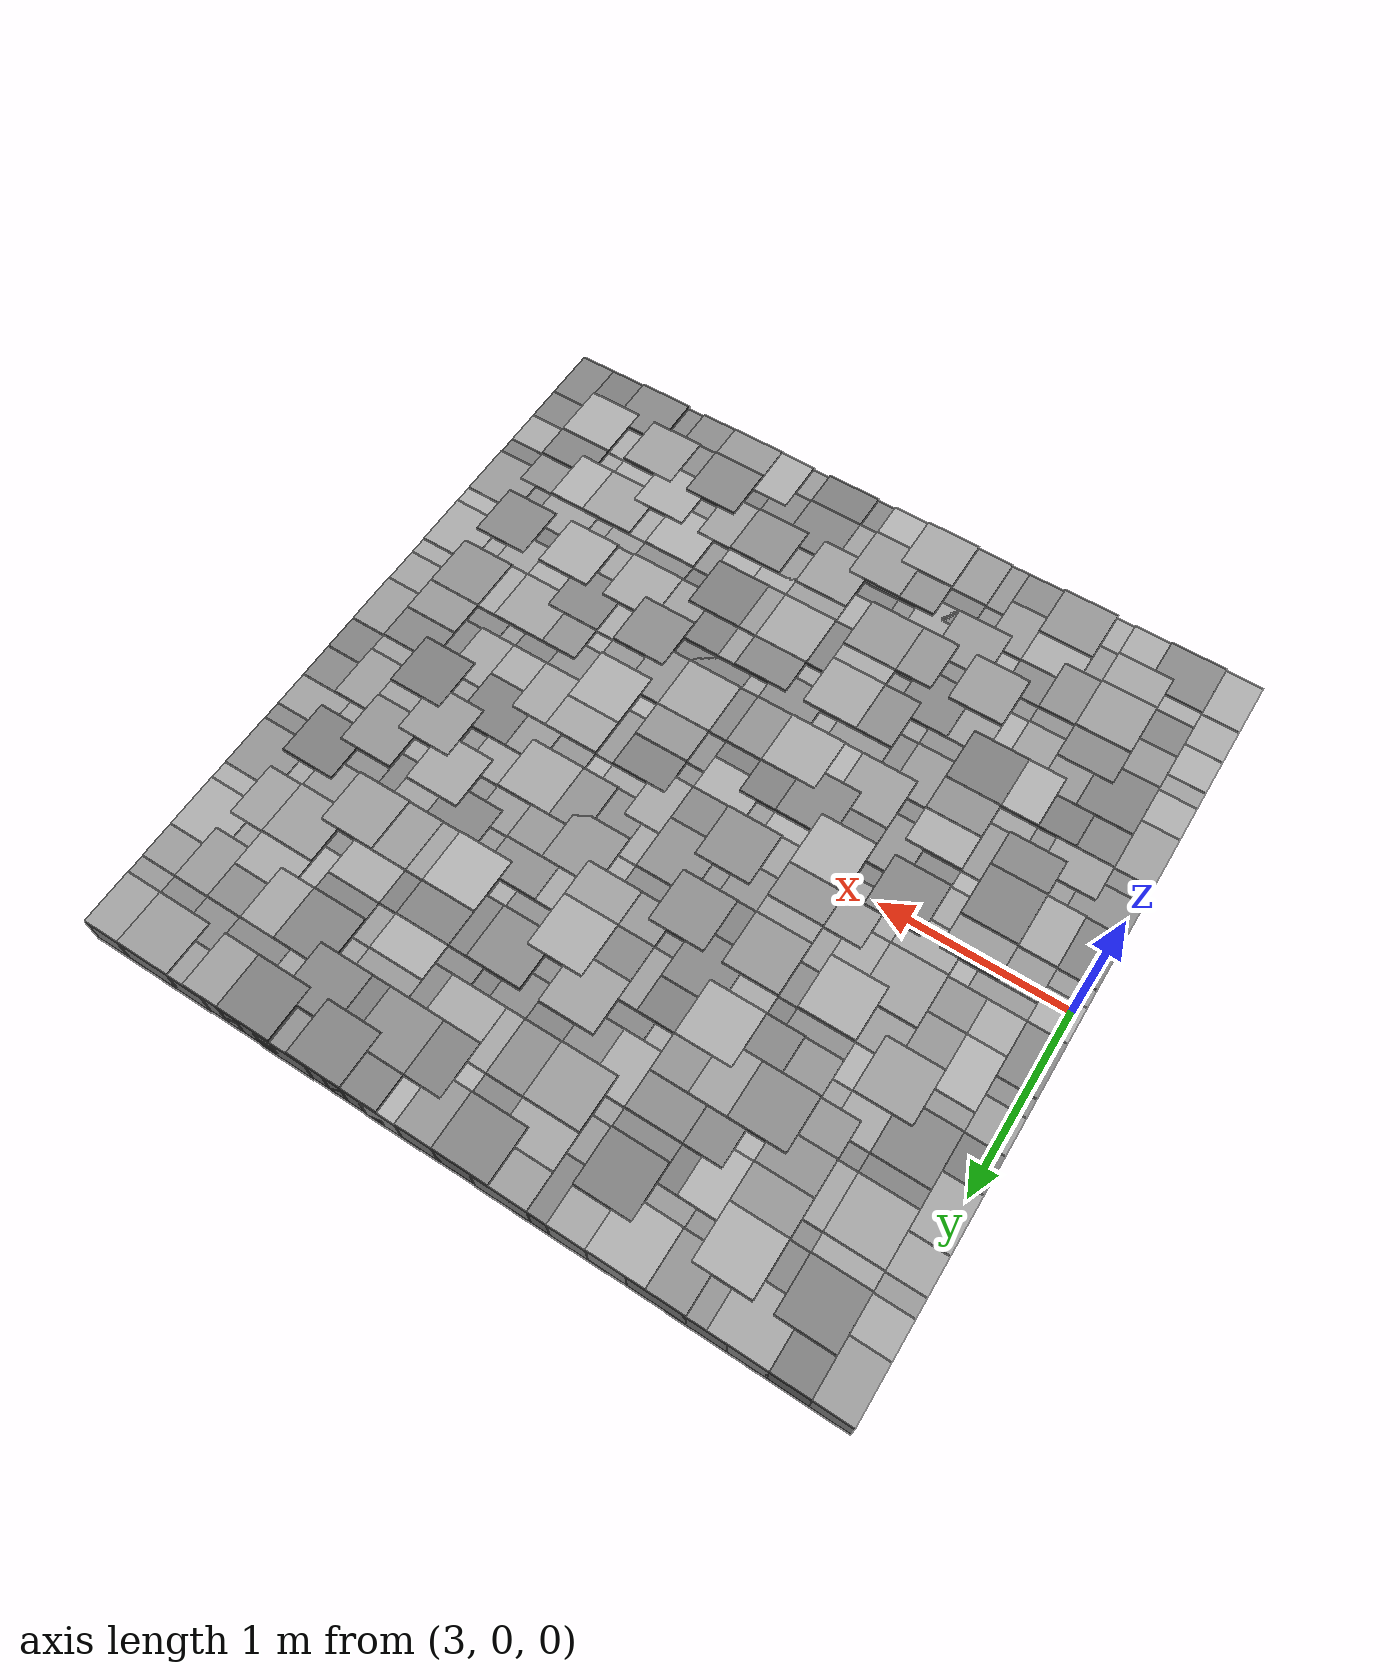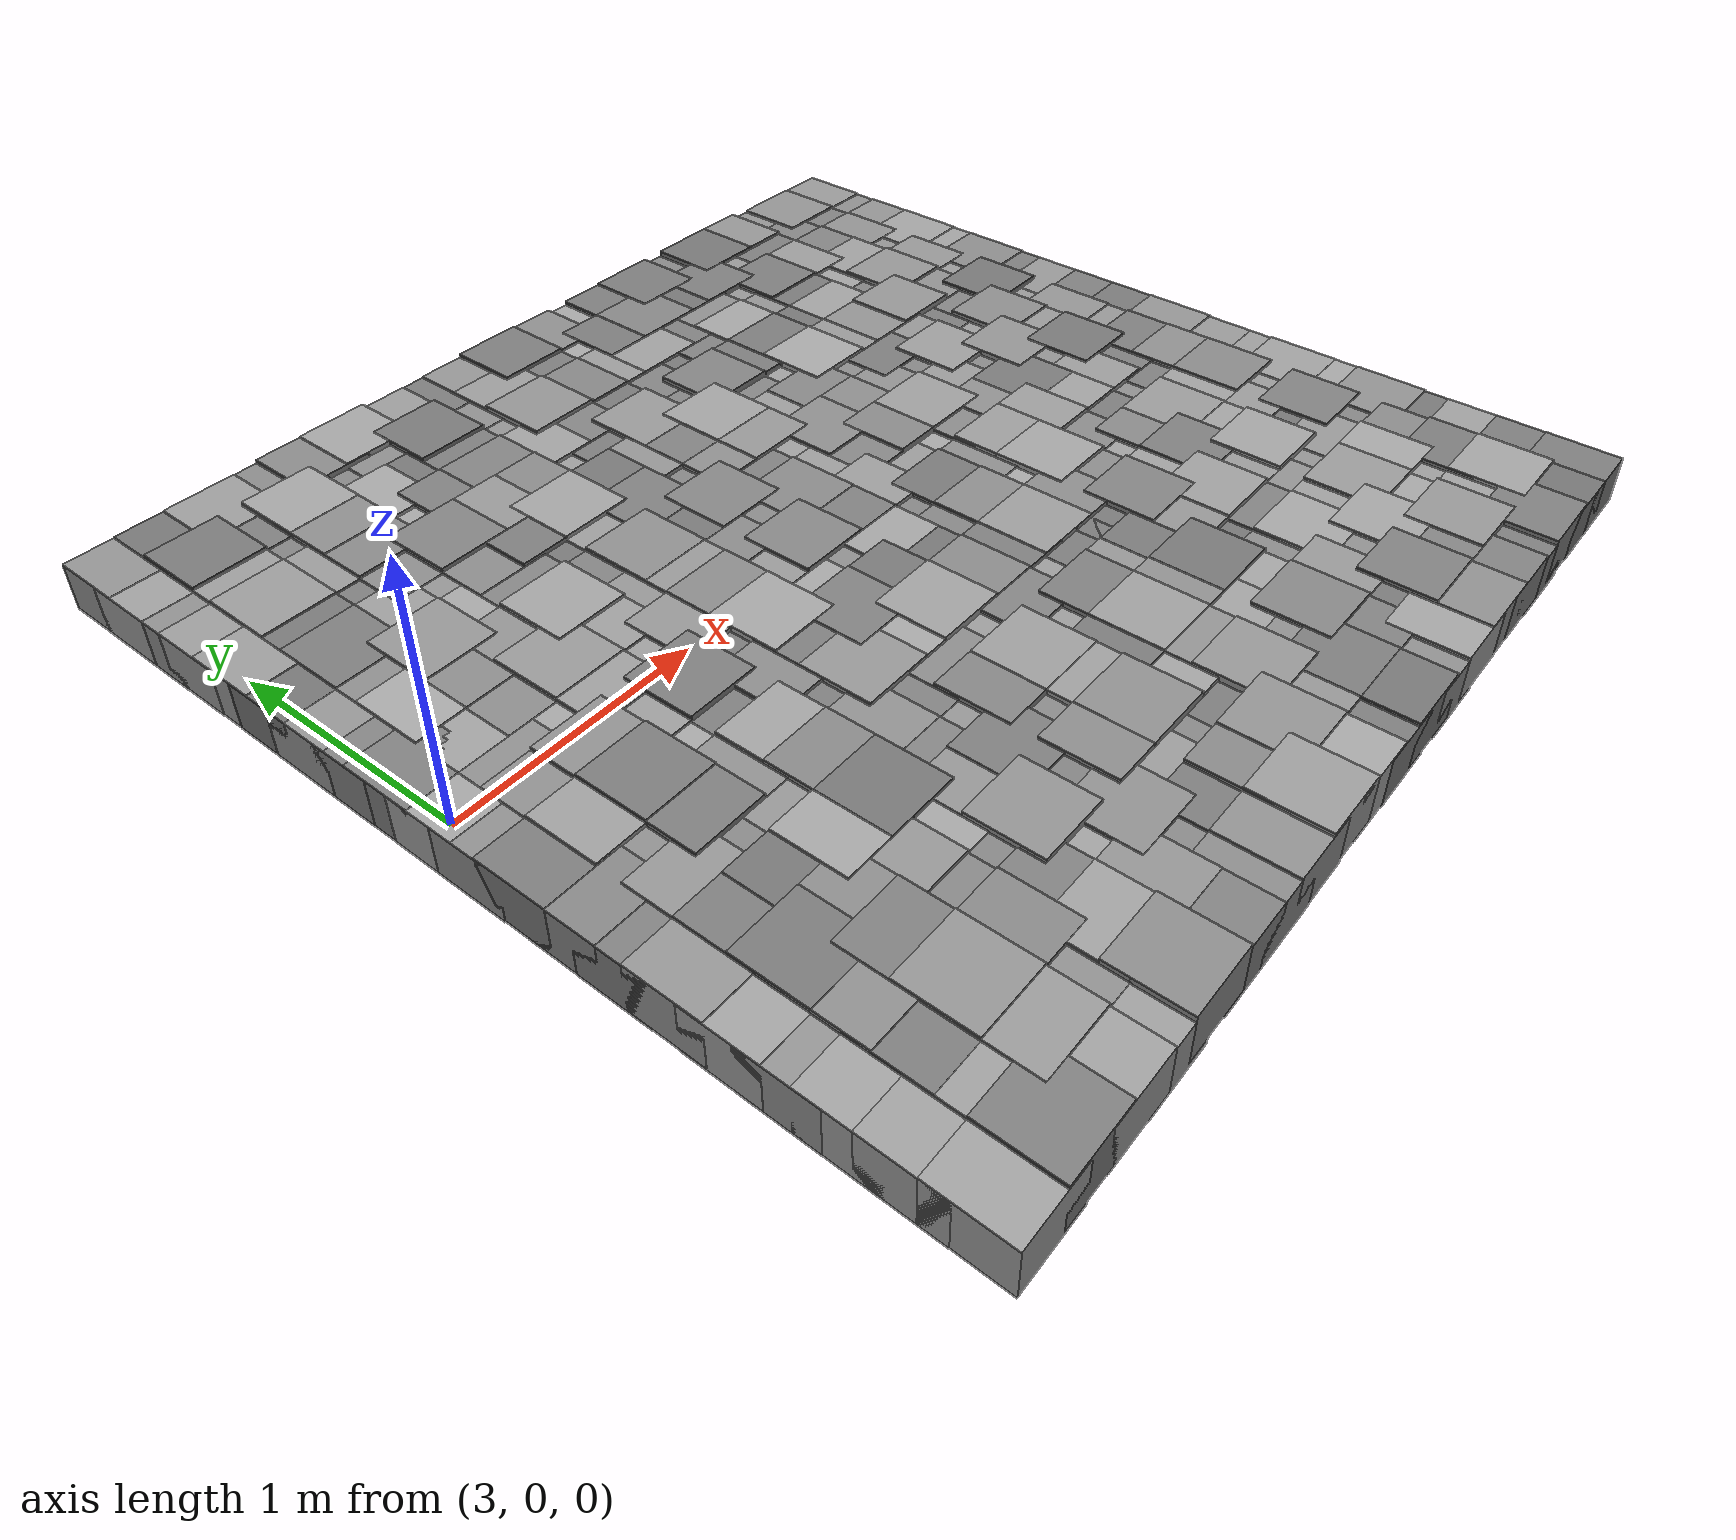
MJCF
<mujoco model="hills">
  <worldbody>
    <geom name="hill_0" type="box" size="0.15 0.15 0.1" pos="3.1000 -1.9000 -0.0953" rgba="0.629 0.629 0.629 1" friction="1.8 0.5 0.5" condim="4"/>
    <geom name="hill_1" type="box" size="0.15 0.15 0.1" pos="3.3000 -1.9000 -0.0825" rgba="0.495 0.495 0.495 1" friction="1.8 0.5 0.5" condim="4"/>
    <geom name="hill_2" type="box" size="0.15 0.15 0.1" pos="3.5000 -1.9000 -0.0910" rgba="0.625 0.625 0.625 1" friction="1.8 0.5 0.5" condim="4"/>
    <geom name="hill_3" type="box" size="0.15 0.15 0.1" pos="3.7000 -1.9000 -0.0998" rgba="0.614 0.614 0.614 1" friction="1.8 0.5 0.5" condim="4"/>
    <geom name="hill_4" type="box" size="0.15 0.15 0.1" pos="3.9000 -1.9000 -0.0761" rgba="0.544 0.544 0.544 1" friction="1.8 0.5 0.5" condim="4"/>
    <geom name="hill_5" type="box" size="0.15 0.15 0.1" pos="4.1000 -1.9000 -0.0909" rgba="0.506 0.506 0.506 1" friction="1.8 0.5 0.5" condim="4"/>
    <geom name="hill_6" type="box" size="0.15 0.15 0.1" pos="4.3000 -1.9000 -0.0924" rgba="0.539 0.539 0.539 1" friction="1.8 0.5 0.5" condim="4"/>
    <geom name="hill_7" type="box" size="0.15 0.15 0.1" pos="4.5000 -1.9000 -0.0849" rgba="0.561 0.561 0.561 1" friction="1.8 0.5 0.5" condim="4"/>
    <geom name="hill_8" type="box" size="0.15 0.15 0.1" pos="4.7000 -1.9000 -0.0701" rgba="0.609 0.609 0.609 1" friction="1.8 0.5 0.5" condim="4"/>
    <geom name="hill_9" type="box" size="0.15 0.15 0.1" pos="4.9000 -1.9000 -0.0813" rgba="0.648 0.648 0.648 1" friction="1.8 0.5 0.5" condim="4"/>
    <geom name="hill_10" type="box" size="0.15 0.15 0.1" pos="5.1000 -1.9000 -0.0935" rgba="0.482 0.482 0.482 1" friction="1.8 0.5 0.5" condim="4"/>
    <geom name="hill_11" type="box" size="0.15 0.15 0.1" pos="5.3000 -1.9000 -0.0816" rgba="0.459 0.459 0.459 1" friction="1.8 0.5 0.5" condim="4"/>
    <geom name="hill_12" type="box" size="0.15 0.15 0.1" pos="5.5000 -1.9000 -0.0989" rgba="0.553 0.553 0.553 1" friction="1.8 0.5 0.5" condim="4"/>
    <geom name="hill_13" type="box" size="0.15 0.15 0.1" pos="5.7000 -1.9000 -0.0860" rgba="0.633 0.633 0.633 1" friction="1.8 0.5 0.5" condim="4"/>
    <geom name="hill_14" type="box" size="0.15 0.15 0.1" pos="5.9000 -1.9000 -0.0811" rgba="0.553 0.553 0.553 1" friction="1.8 0.5 0.5" condim="4"/>
    <geom name="hill_15" type="box" size="0.15 0.15 0.1" pos="6.1000 -1.9000 -0.0851" rgba="0.500 0.500 0.500 1" friction="1.8 0.5 0.5" condim="4"/>
    <geom name="hill_16" type="box" size="0.15 0.15 0.1" pos="6.3000 -1.9000 -0.0996" rgba="0.488 0.488 0.488 1" friction="1.8 0.5 0.5" condim="4"/>
    <geom name="hill_17" type="box" size="0.15 0.15 0.1" pos="6.5000 -1.9000 -0.0792" rgba="0.490 0.490 0.490 1" friction="1.8 0.5 0.5" condim="4"/>
    <geom name="hill_18" type="box" size="0.15 0.15 0.1" pos="6.7000 -1.9000 -0.0917" rgba="0.451 0.451 0.451 1" friction="1.8 0.5 0.5" condim="4"/>
    <geom name="hill_19" type="box" size="0.15 0.15 0.1" pos="6.9000 -1.9000 -0.0938" rgba="0.481 0.481 0.481 1" friction="1.8 0.5 0.5" condim="4"/>
    <geom name="hill_20" type="box" size="0.15 0.15 0.1" pos="3.1000 -1.7000 -0.0980" rgba="0.626 0.626 0.626 1" friction="1.8 0.5 0.5" condim="4"/>
    <geom name="hill_21" type="box" size="0.15 0.15 0.1" pos="3.3000 -1.7000 -0.0885" rgba="0.619 0.619 0.619 1" friction="1.8 0.5 0.5" condim="4"/>
    <geom name="hill_22" type="box" size="0.15 0.15 0.1" pos="3.5000 -1.7000 -0.0808" rgba="0.598 0.598 0.598 1" friction="1.8 0.5 0.5" condim="4"/>
    <geom name="hill_23" type="box" size="0.15 0.15 0.1" pos="3.7000 -1.7000 -0.0973" rgba="0.558 0.558 0.558 1" friction="1.8 0.5 0.5" condim="4"/>
    <geom name="hill_24" type="box" size="0.15 0.15 0.1" pos="3.9000 -1.7000 -0.0848" rgba="0.624 0.624 0.624 1" friction="1.8 0.5 0.5" condim="4"/>
    <geom name="hill_25" type="box" size="0.15 0.15 0.1" pos="4.1000 -1.7000 -0.0892" rgba="0.570 0.570 0.570 1" friction="1.8 0.5 0.5" condim="4"/>
    <geom name="hill_26" type="box" size="0.15 0.15 0.1" pos="4.3000 -1.7000 -0.0982" rgba="0.528 0.528 0.528 1" friction="1.8 0.5 0.5" condim="4"/>
    <geom name="hill_27" type="box" size="0.15 0.15 0.1" pos="4.5000 -1.7000 -0.0903" rgba="0.480 0.480 0.480 1" friction="1.8 0.5 0.5" condim="4"/>
    <geom name="hill_28" type="box" size="0.15 0.15 0.1" pos="4.7000 -1.7000 -0.0755" rgba="0.526 0.526 0.526 1" friction="1.8 0.5 0.5" condim="4"/>
    <geom name="hill_29" type="box" size="0.15 0.15 0.1" pos="4.9000 -1.7000 -0.0706" rgba="0.568 0.568 0.568 1" friction="1.8 0.5 0.5" condim="4"/>
    <geom name="hill_30" type="box" size="0.15 0.15 0.1" pos="5.1000 -1.7000 -0.0818" rgba="0.578 0.578 0.578 1" friction="1.8 0.5 0.5" condim="4"/>
    <geom name="hill_31" type="box" size="0.15 0.15 0.1" pos="5.3000 -1.7000 -0.0797" rgba="0.480 0.480 0.480 1" friction="1.8 0.5 0.5" condim="4"/>
    <geom name="hill_32" type="box" size="0.15 0.15 0.1" pos="5.5000 -1.7000 -0.0868" rgba="0.498 0.498 0.498 1" friction="1.8 0.5 0.5" condim="4"/>
    <geom name="hill_33" type="box" size="0.15 0.15 0.1" pos="5.7000 -1.7000 -0.0879" rgba="0.469 0.469 0.469 1" friction="1.8 0.5 0.5" condim="4"/>
    <geom name="hill_34" type="box" size="0.15 0.15 0.1" pos="5.9000 -1.7000 -0.0710" rgba="0.493 0.493 0.493 1" friction="1.8 0.5 0.5" condim="4"/>
    <geom name="hill_35" type="box" size="0.15 0.15 0.1" pos="6.1000 -1.7000 -0.0798" rgba="0.510 0.510 0.510 1" friction="1.8 0.5 0.5" condim="4"/>
    <geom name="hill_36" type="box" size="0.15 0.15 0.1" pos="6.3000 -1.7000 -0.0738" rgba="0.582 0.582 0.582 1" friction="1.8 0.5 0.5" condim="4"/>
    <geom name="hill_37" type="box" size="0.15 0.15 0.1" pos="6.5000 -1.7000 -0.0961" rgba="0.619 0.619 0.619 1" friction="1.8 0.5 0.5" condim="4"/>
    <geom name="hill_38" type="box" size="0.15 0.15 0.1" pos="6.7000 -1.7000 -0.0787" rgba="0.631 0.631 0.631 1" friction="1.8 0.5 0.5" condim="4"/>
    <geom name="hill_39" type="box" size="0.15 0.15 0.1" pos="6.9000 -1.7000 -0.0957" rgba="0.479 0.479 0.479 1" friction="1.8 0.5 0.5" condim="4"/>
    <geom name="hill_40" type="box" size="0.15 0.15 0.1" pos="3.1000 -1.5000 -0.0986" rgba="0.636 0.636 0.636 1" friction="1.8 0.5 0.5" condim="4"/>
    <geom name="hill_41" type="box" size="0.15 0.15 0.1" pos="3.3000 -1.5000 -0.0876" rgba="0.486 0.486 0.486 1" friction="1.8 0.5 0.5" condim="4"/>
    <geom name="hill_42" type="box" size="0.15 0.15 0.1" pos="3.5000 -1.5000 -0.0735" rgba="0.578 0.578 0.578 1" friction="1.8 0.5 0.5" condim="4"/>
    <geom name="hill_43" type="box" size="0.15 0.15 0.1" pos="3.7000 -1.5000 -0.0829" rgba="0.525 0.525 0.525 1" friction="1.8 0.5 0.5" condim="4"/>
    <geom name="hill_44" type="box" size="0.15 0.15 0.1" pos="3.9000 -1.5000 -0.0877" rgba="0.498 0.498 0.498 1" friction="1.8 0.5 0.5" condim="4"/>
    <geom name="hill_45" type="box" size="0.15 0.15 0.1" pos="4.1000 -1.5000 -0.0989" rgba="0.625 0.625 0.625 1" friction="1.8 0.5 0.5" condim="4"/>
    <geom name="hill_46" type="box" size="0.15 0.15 0.1" pos="4.3000 -1.5000 -0.0860" rgba="0.560 0.560 0.560 1" friction="1.8 0.5 0.5" condim="4"/>
    <geom name="hill_47" type="box" size="0.15 0.15 0.1" pos="4.5000 -1.5000 -0.0903" rgba="0.600 0.600 0.600 1" friction="1.8 0.5 0.5" condim="4"/>
    <geom name="hill_48" type="box" size="0.15 0.15 0.1" pos="4.7000 -1.5000 -0.0992" rgba="0.524 0.524 0.524 1" friction="1.8 0.5 0.5" condim="4"/>
    <geom name="hill_49" type="box" size="0.15 0.15 0.1" pos="4.9000 -1.5000 -0.0991" rgba="0.475 0.475 0.475 1" friction="1.8 0.5 0.5" condim="4"/>
    <geom name="hill_50" type="box" size="0.15 0.15 0.1" pos="5.1000 -1.5000 -0.0710" rgba="0.582 0.582 0.582 1" friction="1.8 0.5 0.5" condim="4"/>
    <geom name="hill_51" type="box" size="0.15 0.15 0.1" pos="5.3000 -1.5000 -0.0872" rgba="0.555 0.555 0.555 1" friction="1.8 0.5 0.5" condim="4"/>
    <geom name="hill_52" type="box" size="0.15 0.15 0.1" pos="5.5000 -1.5000 -0.0738" rgba="0.519 0.519 0.519 1" friction="1.8 0.5 0.5" condim="4"/>
    <geom name="hill_53" type="box" size="0.15 0.15 0.1" pos="5.7000 -1.5000 -0.0823" rgba="0.587 0.587 0.587 1" friction="1.8 0.5 0.5" condim="4"/>
    <geom name="hill_54" type="box" size="0.15 0.15 0.1" pos="5.9000 -1.5000 -0.0893" rgba="0.554 0.554 0.554 1" friction="1.8 0.5 0.5" condim="4"/>
    <geom name="hill_55" type="box" size="0.15 0.15 0.1" pos="6.1000 -1.5000 -0.0770" rgba="0.632 0.632 0.632 1" friction="1.8 0.5 0.5" condim="4"/>
    <geom name="hill_56" type="box" size="0.15 0.15 0.1" pos="6.3000 -1.5000 -0.0955" rgba="0.637 0.637 0.637 1" friction="1.8 0.5 0.5" condim="4"/>
    <geom name="hill_57" type="box" size="0.15 0.15 0.1" pos="6.5000 -1.5000 -0.0998" rgba="0.601 0.601 0.601 1" friction="1.8 0.5 0.5" condim="4"/>
    <geom name="hill_58" type="box" size="0.15 0.15 0.1" pos="6.7000 -1.5000 -0.0818" rgba="0.477 0.477 0.477 1" friction="1.8 0.5 0.5" condim="4"/>
    <geom name="hill_59" type="box" size="0.15 0.15 0.1" pos="6.9000 -1.5000 -0.0969" rgba="0.613 0.613 0.613 1" friction="1.8 0.5 0.5" condim="4"/>
    <geom name="hill_60" type="box" size="0.15 0.15 0.1" pos="3.1000 -1.3000 -0.0999" rgba="0.576 0.576 0.576 1" friction="1.8 0.5 0.5" condim="4"/>
    <geom name="hill_61" type="box" size="0.15 0.15 0.1" pos="3.3000 -1.3000 -0.0822" rgba="0.553 0.553 0.553 1" friction="1.8 0.5 0.5" condim="4"/>
    <geom name="hill_62" type="box" size="0.15 0.15 0.1" pos="3.5000 -1.3000 -0.0782" rgba="0.495 0.495 0.495 1" friction="1.8 0.5 0.5" condim="4"/>
    <geom name="hill_63" type="box" size="0.15 0.15 0.1" pos="3.7000 -1.3000 -0.0940" rgba="0.523 0.523 0.523 1" friction="1.8 0.5 0.5" condim="4"/>
    <geom name="hill_64" type="box" size="0.15 0.15 0.1" pos="3.9000 -1.3000 -0.0946" rgba="0.519 0.519 0.519 1" friction="1.8 0.5 0.5" condim="4"/>
    <geom name="hill_65" type="box" size="0.15 0.15 0.1" pos="4.1000 -1.3000 -0.0716" rgba="0.565 0.565 0.565 1" friction="1.8 0.5 0.5" condim="4"/>
    <geom name="hill_66" type="box" size="0.15 0.15 0.1" pos="4.3000 -1.3000 -0.0898" rgba="0.504 0.504 0.504 1" friction="1.8 0.5 0.5" condim="4"/>
    <geom name="hill_67" type="box" size="0.15 0.15 0.1" pos="4.5000 -1.3000 -0.0714" rgba="0.539 0.539 0.539 1" friction="1.8 0.5 0.5" condim="4"/>
    <geom name="hill_68" type="box" size="0.15 0.15 0.1" pos="4.7000 -1.3000 -0.0706" rgba="0.553 0.553 0.553 1" friction="1.8 0.5 0.5" condim="4"/>
    <geom name="hill_69" type="box" size="0.15 0.15 0.1" pos="4.9000 -1.3000 -0.0844" rgba="0.629 0.629 0.629 1" friction="1.8 0.5 0.5" condim="4"/>
    <geom name="hill_70" type="box" size="0.15 0.15 0.1" pos="5.1000 -1.3000 -0.0777" rgba="0.566 0.566 0.566 1" friction="1.8 0.5 0.5" condim="4"/>
    <geom name="hill_71" type="box" size="0.15 0.15 0.1" pos="5.3000 -1.3000 -0.0872" rgba="0.626 0.626 0.626 1" friction="1.8 0.5 0.5" condim="4"/>
    <geom name="hill_72" type="box" size="0.15 0.15 0.1" pos="5.5000 -1.3000 -0.0877" rgba="0.635 0.635 0.635 1" friction="1.8 0.5 0.5" condim="4"/>
    <geom name="hill_73" type="box" size="0.15 0.15 0.1" pos="5.7000 -1.3000 -0.0979" rgba="0.536 0.536 0.536 1" friction="1.8 0.5 0.5" condim="4"/>
    <geom name="hill_74" type="box" size="0.15 0.15 0.1" pos="5.9000 -1.3000 -0.0844" rgba="0.640 0.640 0.640 1" friction="1.8 0.5 0.5" condim="4"/>
    <geom name="hill_75" type="box" size="0.15 0.15 0.1" pos="6.1000 -1.3000 -0.0925" rgba="0.611 0.611 0.611 1" friction="1.8 0.5 0.5" condim="4"/>
    <geom name="hill_76" type="box" size="0.15 0.15 0.1" pos="6.3000 -1.3000 -0.0797" rgba="0.593 0.593 0.593 1" friction="1.8 0.5 0.5" condim="4"/>
    <geom name="hill_77" type="box" size="0.15 0.15 0.1" pos="6.5000 -1.3000 -0.0811" rgba="0.644 0.644 0.644 1" friction="1.8 0.5 0.5" condim="4"/>
    <geom name="hill_78" type="box" size="0.15 0.15 0.1" pos="6.7000 -1.3000 -0.0925" rgba="0.530 0.530 0.530 1" friction="1.8 0.5 0.5" condim="4"/>
    <geom name="hill_79" type="box" size="0.15 0.15 0.1" pos="6.9000 -1.3000 -0.0985" rgba="0.460 0.460 0.460 1" friction="1.8 0.5 0.5" condim="4"/>
    <geom name="hill_80" type="box" size="0.15 0.15 0.1" pos="3.1000 -1.1000 -0.0984" rgba="0.633 0.633 0.633 1" friction="1.8 0.5 0.5" condim="4"/>
    <geom name="hill_81" type="box" size="0.15 0.15 0.1" pos="3.3000 -1.1000 -0.0811" rgba="0.472 0.472 0.472 1" friction="1.8 0.5 0.5" condim="4"/>
    <geom name="hill_82" type="box" size="0.15 0.15 0.1" pos="3.5000 -1.1000 -0.0819" rgba="0.546 0.546 0.546 1" friction="1.8 0.5 0.5" condim="4"/>
    <geom name="hill_83" type="box" size="0.15 0.15 0.1" pos="3.7000 -1.1000 -0.0822" rgba="0.582 0.582 0.582 1" friction="1.8 0.5 0.5" condim="4"/>
    <geom name="hill_84" type="box" size="0.15 0.15 0.1" pos="3.9000 -1.1000 -0.0908" rgba="0.642 0.642 0.642 1" friction="1.8 0.5 0.5" condim="4"/>
    <geom name="hill_85" type="box" size="0.15 0.15 0.1" pos="4.1000 -1.1000 -0.0860" rgba="0.576 0.576 0.576 1" friction="1.8 0.5 0.5" condim="4"/>
    <geom name="hill_86" type="box" size="0.15 0.15 0.1" pos="4.3000 -1.1000 -0.0809" rgba="0.487 0.487 0.487 1" friction="1.8 0.5 0.5" condim="4"/>
    <geom name="hill_87" type="box" size="0.15 0.15 0.1" pos="4.5000 -1.1000 -0.0981" rgba="0.532 0.532 0.532 1" friction="1.8 0.5 0.5" condim="4"/>
    <geom name="hill_88" type="box" size="0.15 0.15 0.1" pos="4.7000 -1.1000 -0.0771" rgba="0.613 0.613 0.613 1" friction="1.8 0.5 0.5" condim="4"/>
    <geom name="hill_89" type="box" size="0.15 0.15 0.1" pos="4.9000 -1.1000 -0.0781" rgba="0.473 0.473 0.473 1" friction="1.8 0.5 0.5" condim="4"/>
    <geom name="hill_90" type="box" size="0.15 0.15 0.1" pos="5.1000 -1.1000 -0.0726" rgba="0.610 0.610 0.610 1" friction="1.8 0.5 0.5" condim="4"/>
    <geom name="hill_91" type="box" size="0.15 0.15 0.1" pos="5.3000 -1.1000 -0.0737" rgba="0.555 0.555 0.555 1" friction="1.8 0.5 0.5" condim="4"/>
    <geom name="hill_92" type="box" size="0.15 0.15 0.1" pos="5.5000 -1.1000 -0.0725" rgba="0.459 0.459 0.459 1" friction="1.8 0.5 0.5" condim="4"/>
    <geom name="hill_93" type="box" size="0.15 0.15 0.1" pos="5.7000 -1.1000 -0.0991" rgba="0.454 0.454 0.454 1" friction="1.8 0.5 0.5" condim="4"/>
    <geom name="hill_94" type="box" size="0.15 0.15 0.1" pos="5.9000 -1.1000 -0.0924" rgba="0.500 0.500 0.500 1" friction="1.8 0.5 0.5" condim="4"/>
    <geom name="hill_95" type="box" size="0.15 0.15 0.1" pos="6.1000 -1.1000 -0.0944" rgba="0.563 0.563 0.563 1" friction="1.8 0.5 0.5" condim="4"/>
    <geom name="hill_96" type="box" size="0.15 0.15 0.1" pos="6.3000 -1.1000 -0.0988" rgba="0.568 0.568 0.568 1" friction="1.8 0.5 0.5" condim="4"/>
    <geom name="hill_97" type="box" size="0.15 0.15 0.1" pos="6.5000 -1.1000 -0.0950" rgba="0.586 0.586 0.586 1" friction="1.8 0.5 0.5" condim="4"/>
    <geom name="hill_98" type="box" size="0.15 0.15 0.1" pos="6.7000 -1.1000 -0.0995" rgba="0.512 0.512 0.512 1" friction="1.8 0.5 0.5" condim="4"/>
    <geom name="hill_99" type="box" size="0.15 0.15 0.1" pos="6.9000 -1.1000 -0.0930" rgba="0.558 0.558 0.558 1" friction="1.8 0.5 0.5" condim="4"/>
    <geom name="hill_100" type="box" size="0.15 0.15 0.1" pos="3.1000 -0.9000 -0.0939" rgba="0.582 0.582 0.582 1" friction="1.8 0.5 0.5" condim="4"/>
    <geom name="hill_101" type="box" size="0.15 0.15 0.1" pos="3.3000 -0.9000 -0.0863" rgba="0.488 0.488 0.488 1" friction="1.8 0.5 0.5" condim="4"/>
    <geom name="hill_102" type="box" size="0.15 0.15 0.1" pos="3.5000 -0.9000 -0.0828" rgba="0.458 0.458 0.458 1" friction="1.8 0.5 0.5" condim="4"/>
    <geom name="hill_103" type="box" size="0.15 0.15 0.1" pos="3.7000 -0.9000 -0.0760" rgba="0.642 0.642 0.642 1" friction="1.8 0.5 0.5" condim="4"/>
    <geom name="hill_104" type="box" size="0.15 0.15 0.1" pos="3.9000 -0.9000 -0.0744" rgba="0.460 0.460 0.460 1" friction="1.8 0.5 0.5" condim="4"/>
    <geom name="hill_105" type="box" size="0.15 0.15 0.1" pos="4.1000 -0.9000 -0.0898" rgba="0.514 0.514 0.514 1" friction="1.8 0.5 0.5" condim="4"/>
    <geom name="hill_106" type="box" size="0.15 0.15 0.1" pos="4.3000 -0.9000 -0.0966" rgba="0.575 0.575 0.575 1" friction="1.8 0.5 0.5" condim="4"/>
    <geom name="hill_107" type="box" size="0.15 0.15 0.1" pos="4.5000 -0.9000 -0.0761" rgba="0.513 0.513 0.513 1" friction="1.8 0.5 0.5" condim="4"/>
    <geom name="hill_108" type="box" size="0.15 0.15 0.1" pos="4.7000 -0.9000 -0.0741" rgba="0.609 0.609 0.609 1" friction="1.8 0.5 0.5" condim="4"/>
    <geom name="hill_109" type="box" size="0.15 0.15 0.1" pos="4.9000 -0.9000 -0.0961" rgba="0.603 0.603 0.603 1" friction="1.8 0.5 0.5" condim="4"/>
    <geom name="hill_110" type="box" size="0.15 0.15 0.1" pos="5.1000 -0.9000 -0.0735" rgba="0.489 0.489 0.489 1" friction="1.8 0.5 0.5" condim="4"/>
    <geom name="hill_111" type="box" size="0.15 0.15 0.1" pos="5.3000 -0.9000 -0.0828" rgba="0.578 0.578 0.578 1" friction="1.8 0.5 0.5" condim="4"/>
    <geom name="hill_112" type="box" size="0.15 0.15 0.1" pos="5.5000 -0.9000 -0.0817" rgba="0.469 0.469 0.469 1" friction="1.8 0.5 0.5" condim="4"/>
    <geom name="hill_113" type="box" size="0.15 0.15 0.1" pos="5.7000 -0.9000 -0.0802" rgba="0.576 0.576 0.576 1" friction="1.8 0.5 0.5" condim="4"/>
    <geom name="hill_114" type="box" size="0.15 0.15 0.1" pos="5.9000 -0.9000 -0.0753" rgba="0.611 0.611 0.611 1" friction="1.8 0.5 0.5" condim="4"/>
    <geom name="hill_115" type="box" size="0.15 0.15 0.1" pos="6.1000 -0.9000 -0.0902" rgba="0.594 0.594 0.594 1" friction="1.8 0.5 0.5" condim="4"/>
    <geom name="hill_116" type="box" size="0.15 0.15 0.1" pos="6.3000 -0.9000 -0.0740" rgba="0.629 0.629 0.629 1" friction="1.8 0.5 0.5" condim="4"/>
    <geom name="hill_117" type="box" size="0.15 0.15 0.1" pos="6.5000 -0.9000 -0.0952" rgba="0.455 0.455 0.455 1" friction="1.8 0.5 0.5" condim="4"/>
    <geom name="hill_118" type="box" size="0.15 0.15 0.1" pos="6.7000 -0.9000 -0.0854" rgba="0.493 0.493 0.493 1" friction="1.8 0.5 0.5" condim="4"/>
    <geom name="hill_119" type="box" size="0.15 0.15 0.1" pos="6.9000 -0.9000 -0.0958" rgba="0.639 0.639 0.639 1" friction="1.8 0.5 0.5" condim="4"/>
    <geom name="hill_120" type="box" size="0.15 0.15 0.1" pos="3.1000 -0.7000 -0.0972" rgba="0.501 0.501 0.501 1" friction="1.8 0.5 0.5" condim="4"/>
    <geom name="hill_121" type="box" size="0.15 0.15 0.1" pos="3.3000 -0.7000 -0.0897" rgba="0.581 0.581 0.581 1" friction="1.8 0.5 0.5" condim="4"/>
    <geom name="hill_122" type="box" size="0.15 0.15 0.1" pos="3.5000 -0.7000 -0.0970" rgba="0.526 0.526 0.526 1" friction="1.8 0.5 0.5" condim="4"/>
    <geom name="hill_123" type="box" size="0.15 0.15 0.1" pos="3.7000 -0.7000 -0.0960" rgba="0.582 0.582 0.582 1" friction="1.8 0.5 0.5" condim="4"/>
    <geom name="hill_124" type="box" size="0.15 0.15 0.1" pos="3.9000 -0.7000 -0.0751" rgba="0.525 0.525 0.525 1" friction="1.8 0.5 0.5" condim="4"/>
    <geom name="hill_125" type="box" size="0.15 0.15 0.1" pos="4.1000 -0.7000 -0.0888" rgba="0.558 0.558 0.558 1" friction="1.8 0.5 0.5" condim="4"/>
    <geom name="hill_126" type="box" size="0.15 0.15 0.1" pos="4.3000 -0.7000 -0.0935" rgba="0.499 0.499 0.499 1" friction="1.8 0.5 0.5" condim="4"/>
    <geom name="hill_127" type="box" size="0.15 0.15 0.1" pos="4.5000 -0.7000 -0.0901" rgba="0.541 0.541 0.541 1" friction="1.8 0.5 0.5" condim="4"/>
    <geom name="hill_128" type="box" size="0.15 0.15 0.1" pos="4.7000 -0.7000 -0.0976" rgba="0.601 0.601 0.601 1" friction="1.8 0.5 0.5" condim="4"/>
    <geom name="hill_129" type="box" size="0.15 0.15 0.1" pos="4.9000 -0.7000 -0.0826" rgba="0.510 0.510 0.510 1" friction="1.8 0.5 0.5" condim="4"/>
    <geom name="hill_130" type="box" size="0.15 0.15 0.1" pos="5.1000 -0.7000 -0.0977" rgba="0.603 0.603 0.603 1" friction="1.8 0.5 0.5" condim="4"/>
    <geom name="hill_131" type="box" size="0.15 0.15 0.1" pos="5.3000 -0.7000 -0.0961" rgba="0.477 0.477 0.477 1" friction="1.8 0.5 0.5" condim="4"/>
    <geom name="hill_132" type="box" size="0.15 0.15 0.1" pos="5.5000 -0.7000 -0.0961" rgba="0.466 0.466 0.466 1" friction="1.8 0.5 0.5" condim="4"/>
    <geom name="hill_133" type="box" size="0.15 0.15 0.1" pos="5.7000 -0.7000 -0.0728" rgba="0.504 0.504 0.504 1" friction="1.8 0.5 0.5" condim="4"/>
    <geom name="hill_134" type="box" size="0.15 0.15 0.1" pos="5.9000 -0.7000 -0.0908" rgba="0.617 0.617 0.617 1" friction="1.8 0.5 0.5" condim="4"/>
    <geom name="hill_135" type="box" size="0.15 0.15 0.1" pos="6.1000 -0.7000 -0.0814" rgba="0.487 0.487 0.487 1" friction="1.8 0.5 0.5" condim="4"/>
    <geom name="hill_136" type="box" size="0.15 0.15 0.1" pos="6.3000 -0.7000 -0.0870" rgba="0.627 0.627 0.627 1" friction="1.8 0.5 0.5" condim="4"/>
    <geom name="hill_137" type="box" size="0.15 0.15 0.1" pos="6.5000 -0.7000 -0.0887" rgba="0.592 0.592 0.592 1" friction="1.8 0.5 0.5" condim="4"/>
    <geom name="hill_138" type="box" size="0.15 0.15 0.1" pos="6.7000 -0.7000 -0.0978" rgba="0.595 0.595 0.595 1" friction="1.8 0.5 0.5" condim="4"/>
    <geom name="hill_139" type="box" size="0.15 0.15 0.1" pos="6.9000 -0.7000 -0.0942" rgba="0.615 0.615 0.615 1" friction="1.8 0.5 0.5" condim="4"/>
    <geom name="hill_140" type="box" size="0.15 0.15 0.1" pos="3.1000 -0.5000 -0.0949" rgba="0.524 0.524 0.524 1" friction="1.8 0.5 0.5" condim="4"/>
    <geom name="hill_141" type="box" size="0.15 0.15 0.1" pos="3.3000 -0.5000 -0.0986" rgba="0.554 0.554 0.554 1" friction="1.8 0.5 0.5" condim="4"/>
    <geom name="hill_142" type="box" size="0.15 0.15 0.1" pos="3.5000 -0.5000 -0.0773" rgba="0.488 0.488 0.488 1" friction="1.8 0.5 0.5" condim="4"/>
    <geom name="hill_143" type="box" size="0.15 0.15 0.1" pos="3.7000 -0.5000 -0.0920" rgba="0.557 0.557 0.557 1" friction="1.8 0.5 0.5" condim="4"/>
    <geom name="hill_144" type="box" size="0.15 0.15 0.1" pos="3.9000 -0.5000 -0.0776" rgba="0.629 0.629 0.629 1" friction="1.8 0.5 0.5" condim="4"/>
    <geom name="hill_145" type="box" size="0.15 0.15 0.1" pos="4.1000 -0.5000 -0.0962" rgba="0.487 0.487 0.487 1" friction="1.8 0.5 0.5" condim="4"/>
    <geom name="hill_146" type="box" size="0.15 0.15 0.1" pos="4.3000 -0.5000 -0.0760" rgba="0.579 0.579 0.579 1" friction="1.8 0.5 0.5" condim="4"/>
    <geom name="hill_147" type="box" size="0.15 0.15 0.1" pos="4.5000 -0.5000 -0.0784" rgba="0.649 0.649 0.649 1" friction="1.8 0.5 0.5" condim="4"/>
    <geom name="hill_148" type="box" size="0.15 0.15 0.1" pos="4.7000 -0.5000 -0.0718" rgba="0.619 0.619 0.619 1" friction="1.8 0.5 0.5" condim="4"/>
    <geom name="hill_149" type="box" size="0.15 0.15 0.1" pos="4.9000 -0.5000 -0.0767" rgba="0.529 0.529 0.529 1" friction="1.8 0.5 0.5" condim="4"/>
    <geom name="hill_150" type="box" size="0.15 0.15 0.1" pos="5.1000 -0.5000 -0.0808" rgba="0.487 0.487 0.487 1" friction="1.8 0.5 0.5" condim="4"/>
    <geom name="hill_151" type="box" size="0.15 0.15 0.1" pos="5.3000 -0.5000 -0.0772" rgba="0.602 0.602 0.602 1" friction="1.8 0.5 0.5" condim="4"/>
    <geom name="hill_152" type="box" size="0.15 0.15 0.1" pos="5.5000 -0.5000 -0.0784" rgba="0.539 0.539 0.539 1" friction="1.8 0.5 0.5" condim="4"/>
    <geom name="hill_153" type="box" size="0.15 0.15 0.1" pos="5.7000 -0.5000 -0.0887" rgba="0.534 0.534 0.534 1" friction="1.8 0.5 0.5" condim="4"/>
    <geom name="hill_154" type="box" size="0.15 0.15 0.1" pos="5.9000 -0.5000 -0.0990" rgba="0.619 0.619 0.619 1" friction="1.8 0.5 0.5" condim="4"/>
    <geom name="hill_155" type="box" size="0.15 0.15 0.1" pos="6.1000 -0.5000 -0.0837" rgba="0.528 0.528 0.528 1" friction="1.8 0.5 0.5" condim="4"/>
    <geom name="hill_156" type="box" size="0.15 0.15 0.1" pos="6.3000 -0.5000 -0.0836" rgba="0.594 0.594 0.594 1" friction="1.8 0.5 0.5" condim="4"/>
    <geom name="hill_157" type="box" size="0.15 0.15 0.1" pos="6.5000 -0.5000 -0.0886" rgba="0.616 0.616 0.616 1" friction="1.8 0.5 0.5" condim="4"/>
    <geom name="hill_158" type="box" size="0.15 0.15 0.1" pos="6.7000 -0.5000 -0.0793" rgba="0.527 0.527 0.527 1" friction="1.8 0.5 0.5" condim="4"/>
    <geom name="hill_159" type="box" size="0.15 0.15 0.1" pos="6.9000 -0.5000 -0.0990" rgba="0.602 0.602 0.602 1" friction="1.8 0.5 0.5" condim="4"/>
    <geom name="hill_160" type="box" size="0.15 0.15 0.1" pos="3.1000 -0.3000 -0.0926" rgba="0.480 0.480 0.480 1" friction="1.8 0.5 0.5" condim="4"/>
    <geom name="hill_161" type="box" size="0.15 0.15 0.1" pos="3.3000 -0.3000 -0.0840" rgba="0.615 0.615 0.615 1" friction="1.8 0.5 0.5" condim="4"/>
    <geom name="hill_162" type="box" size="0.15 0.15 0.1" pos="3.5000 -0.3000 -0.0724" rgba="0.475 0.475 0.475 1" friction="1.8 0.5 0.5" condim="4"/>
    <geom name="hill_163" type="box" size="0.15 0.15 0.1" pos="3.7000 -0.3000 -0.0972" rgba="0.648 0.648 0.648 1" friction="1.8 0.5 0.5" condim="4"/>
    <geom name="hill_164" type="box" size="0.15 0.15 0.1" pos="3.9000 -0.3000 -0.0965" rgba="0.485 0.485 0.485 1" friction="1.8 0.5 0.5" condim="4"/>
    <geom name="hill_165" type="box" size="0.15 0.15 0.1" pos="4.1000 -0.3000 -0.0828" rgba="0.539 0.539 0.539 1" friction="1.8 0.5 0.5" condim="4"/>
    <geom name="hill_166" type="box" size="0.15 0.15 0.1" pos="4.3000 -0.3000 -0.0775" rgba="0.488 0.488 0.488 1" friction="1.8 0.5 0.5" condim="4"/>
    <geom name="hill_167" type="box" size="0.15 0.15 0.1" pos="4.5000 -0.3000 -0.0726" rgba="0.493 0.493 0.493 1" friction="1.8 0.5 0.5" condim="4"/>
    <geom name="hill_168" type="box" size="0.15 0.15 0.1" pos="4.7000 -0.3000 -0.0769" rgba="0.464 0.464 0.464 1" friction="1.8 0.5 0.5" condim="4"/>
    <geom name="hill_169" type="box" size="0.15 0.15 0.1" pos="4.9000 -0.3000 -0.0858" rgba="0.457 0.457 0.457 1" friction="1.8 0.5 0.5" condim="4"/>
    <geom name="hill_170" type="box" size="0.15 0.15 0.1" pos="5.1000 -0.3000 -0.0906" rgba="0.512 0.512 0.512 1" friction="1.8 0.5 0.5" condim="4"/>
    <geom name="hill_171" type="box" size="0.15 0.15 0.1" pos="5.3000 -0.3000 -0.0784" rgba="0.541 0.541 0.541 1" friction="1.8 0.5 0.5" condim="4"/>
    <geom name="hill_172" type="box" size="0.15 0.15 0.1" pos="5.5000 -0.3000 -0.0983" rgba="0.649 0.649 0.649 1" friction="1.8 0.5 0.5" condim="4"/>
    <geom name="hill_173" type="box" size="0.15 0.15 0.1" pos="5.7000 -0.3000 -0.0733" rgba="0.633 0.633 0.633 1" friction="1.8 0.5 0.5" condim="4"/>
    <geom name="hill_174" type="box" size="0.15 0.15 0.1" pos="5.9000 -0.3000 -0.0926" rgba="0.529 0.529 0.529 1" friction="1.8 0.5 0.5" condim="4"/>
    <geom name="hill_175" type="box" size="0.15 0.15 0.1" pos="6.1000 -0.3000 -0.0932" rgba="0.475 0.475 0.475 1" friction="1.8 0.5 0.5" condim="4"/>
    <geom name="hill_176" type="box" size="0.15 0.15 0.1" pos="6.3000 -0.3000 -0.0990" rgba="0.551 0.551 0.551 1" friction="1.8 0.5 0.5" condim="4"/>
    <geom name="hill_177" type="box" size="0.15 0.15 0.1" pos="6.5000 -0.3000 -0.0963" rgba="0.485 0.485 0.485 1" friction="1.8 0.5 0.5" condim="4"/>
    <geom name="hill_178" type="box" size="0.15 0.15 0.1" pos="6.7000 -0.3000 -0.0806" rgba="0.547 0.547 0.547 1" friction="1.8 0.5 0.5" condim="4"/>
    <geom name="hill_179" type="box" size="0.15 0.15 0.1" pos="6.9000 -0.3000 -0.0986" rgba="0.584 0.584 0.584 1" friction="1.8 0.5 0.5" condim="4"/>
    <geom name="hill_180" type="box" size="0.15 0.15 0.1" pos="3.1000 -0.1000 -0.0980" rgba="0.555 0.555 0.555 1" friction="1.8 0.5 0.5" condim="4"/>
    <geom name="hill_181" type="box" size="0.15 0.15 0.1" pos="3.3000 -0.1000 -0.0936" rgba="0.553 0.553 0.553 1" friction="1.8 0.5 0.5" condim="4"/>
    <geom name="hill_182" type="box" size="0.15 0.15 0.1" pos="3.5000 -0.1000 -0.0811" rgba="0.557 0.557 0.557 1" friction="1.8 0.5 0.5" condim="4"/>
    <geom name="hill_183" type="box" size="0.15 0.15 0.1" pos="3.7000 -0.1000 -0.0881" rgba="0.608 0.608 0.608 1" friction="1.8 0.5 0.5" condim="4"/>
    <geom name="hill_184" type="box" size="0.15 0.15 0.1" pos="3.9000 -0.1000 -0.0738" rgba="0.486 0.486 0.486 1" friction="1.8 0.5 0.5" condim="4"/>
    <geom name="hill_185" type="box" size="0.15 0.15 0.1" pos="4.1000 -0.1000 -0.0959" rgba="0.473 0.473 0.473 1" friction="1.8 0.5 0.5" condim="4"/>
    <geom name="hill_186" type="box" size="0.15 0.15 0.1" pos="4.3000 -0.1000 -0.0706" rgba="0.638 0.638 0.638 1" friction="1.8 0.5 0.5" condim="4"/>
    <geom name="hill_187" type="box" size="0.15 0.15 0.1" pos="4.5000 -0.1000 -0.0931" rgba="0.644 0.644 0.644 1" friction="1.8 0.5 0.5" condim="4"/>
    <geom name="hill_188" type="box" size="0.15 0.15 0.1" pos="4.7000 -0.1000 -0.0938" rgba="0.551 0.551 0.551 1" friction="1.8 0.5 0.5" condim="4"/>
    <geom name="hill_189" type="box" size="0.15 0.15 0.1" pos="4.9000 -0.1000 -0.0851" rgba="0.633 0.633 0.633 1" friction="1.8 0.5 0.5" condim="4"/>
    <geom name="hill_190" type="box" size="0.15 0.15 0.1" pos="5.1000 -0.1000 -0.0988" rgba="0.513 0.513 0.513 1" friction="1.8 0.5 0.5" condim="4"/>
    <geom name="hill_191" type="box" size="0.15 0.15 0.1" pos="5.3000 -0.1000 -0.0820" rgba="0.463 0.463 0.463 1" friction="1.8 0.5 0.5" condim="4"/>
    <geom name="hill_192" type="box" size="0.15 0.15 0.1" pos="5.5000 -0.1000 -0.0929" rgba="0.543 0.543 0.543 1" friction="1.8 0.5 0.5" condim="4"/>
    <geom name="hill_193" type="box" size="0.15 0.15 0.1" pos="5.7000 -0.1000 -0.0736" rgba="0.602 0.602 0.602 1" friction="1.8 0.5 0.5" condim="4"/>
    <geom name="hill_194" type="box" size="0.15 0.15 0.1" pos="5.9000 -0.1000 -0.0751" rgba="0.602 0.602 0.602 1" friction="1.8 0.5 0.5" condim="4"/>
    <geom name="hill_195" type="box" size="0.15 0.15 0.1" pos="6.1000 -0.1000 -0.0788" rgba="0.620 0.620 0.620 1" friction="1.8 0.5 0.5" condim="4"/>
    <geom name="hill_196" type="box" size="0.15 0.15 0.1" pos="6.3000 -0.1000 -0.0796" rgba="0.597 0.597 0.597 1" friction="1.8 0.5 0.5" condim="4"/>
    <geom name="hill_197" type="box" size="0.15 0.15 0.1" pos="6.5000 -0.1000 -0.0910" rgba="0.484 0.484 0.484 1" friction="1.8 0.5 0.5" condim="4"/>
    <geom name="hill_198" type="box" size="0.15 0.15 0.1" pos="6.7000 -0.1000 -0.0830" rgba="0.483 0.483 0.483 1" friction="1.8 0.5 0.5" condim="4"/>
    <geom name="hill_199" type="box" size="0.15 0.15 0.1" pos="6.9000 -0.1000 -0.0931" rgba="0.569 0.569 0.569 1" friction="1.8 0.5 0.5" condim="4"/>
    <geom name="hill_200" type="box" size="0.15 0.15 0.1" pos="3.1000 0.1000 -0.0975" rgba="0.637 0.637 0.637 1" friction="1.8 0.5 0.5" condim="4"/>
    <geom name="hill_201" type="box" size="0.15 0.15 0.1" pos="3.3000 0.1000 -0.0965" rgba="0.553 0.553 0.553 1" friction="1.8 0.5 0.5" condim="4"/>
    <geom name="hill_202" type="box" size="0.15 0.15 0.1" pos="3.5000 0.1000 -0.0973" rgba="0.643 0.643 0.643 1" friction="1.8 0.5 0.5" condim="4"/>
    <geom name="hill_203" type="box" size="0.15 0.15 0.1" pos="3.7000 0.1000 -0.0827" rgba="0.611 0.611 0.611 1" friction="1.8 0.5 0.5" condim="4"/>
    <geom name="hill_204" type="box" size="0.15 0.15 0.1" pos="3.9000 0.1000 -0.0915" rgba="0.610 0.610 0.610 1" friction="1.8 0.5 0.5" condim="4"/>
    <geom name="hill_205" type="box" size="0.15 0.15 0.1" pos="4.1000 0.1000 -0.0789" rgba="0.579 0.579 0.579 1" friction="1.8 0.5 0.5" condim="4"/>
    <geom name="hill_206" type="box" size="0.15 0.15 0.1" pos="4.3000 0.1000 -0.0715" rgba="0.537 0.537 0.537 1" friction="1.8 0.5 0.5" condim="4"/>
    <geom name="hill_207" type="box" size="0.15 0.15 0.1" pos="4.5000 0.1000 -0.0875" rgba="0.588 0.588 0.588 1" friction="1.8 0.5 0.5" condim="4"/>
    <geom name="hill_208" type="box" size="0.15 0.15 0.1" pos="4.7000 0.1000 -0.0749" rgba="0.517 0.517 0.517 1" friction="1.8 0.5 0.5" condim="4"/>
    <geom name="hill_209" type="box" size="0.15 0.15 0.1" pos="4.9000 0.1000 -0.0799" rgba="0.492 0.492 0.492 1" friction="1.8 0.5 0.5" condim="4"/>
    <geom name="hill_210" type="box" size="0.15 0.15 0.1" pos="5.1000 0.1000 -0.0834" rgba="0.604 0.604 0.604 1" friction="1.8 0.5 0.5" condim="4"/>
    <geom name="hill_211" type="box" size="0.15 0.15 0.1" pos="5.3000 0.1000 -0.0980" rgba="0.596 0.596 0.596 1" friction="1.8 0.5 0.5" condim="4"/>
    <geom name="hill_212" type="box" size="0.15 0.15 0.1" pos="5.5000 0.1000 -0.0995" rgba="0.642 0.642 0.642 1" friction="1.8 0.5 0.5" condim="4"/>
    <geom name="hill_213" type="box" size="0.15 0.15 0.1" pos="5.7000 0.1000 -0.0859" rgba="0.532 0.532 0.532 1" friction="1.8 0.5 0.5" condim="4"/>
    <geom name="hill_214" type="box" size="0.15 0.15 0.1" pos="5.9000 0.1000 -0.0784" rgba="0.555 0.555 0.555 1" friction="1.8 0.5 0.5" condim="4"/>
    <geom name="hill_215" type="box" size="0.15 0.15 0.1" pos="6.1000 0.1000 -0.0781" rgba="0.467 0.467 0.467 1" friction="1.8 0.5 0.5" condim="4"/>
    <geom name="hill_216" type="box" size="0.15 0.15 0.1" pos="6.3000 0.1000 -0.0831" rgba="0.562 0.562 0.562 1" friction="1.8 0.5 0.5" condim="4"/>
    <geom name="hill_217" type="box" size="0.15 0.15 0.1" pos="6.5000 0.1000 -0.0720" rgba="0.458 0.458 0.458 1" friction="1.8 0.5 0.5" condim="4"/>
    <geom name="hill_218" type="box" size="0.15 0.15 0.1" pos="6.7000 0.1000 -0.0898" rgba="0.576 0.576 0.576 1" friction="1.8 0.5 0.5" condim="4"/>
    <geom name="hill_219" type="box" size="0.15 0.15 0.1" pos="6.9000 0.1000 -0.0959" rgba="0.465 0.465 0.465 1" friction="1.8 0.5 0.5" condim="4"/>
    <geom name="hill_220" type="box" size="0.15 0.15 0.1" pos="3.1000 0.3000 -0.0956" rgba="0.494 0.494 0.494 1" friction="1.8 0.5 0.5" condim="4"/>
    <geom name="hill_221" type="box" size="0.15 0.15 0.1" pos="3.3000 0.3000 -0.0956" rgba="0.626 0.626 0.626 1" friction="1.8 0.5 0.5" condim="4"/>
    <geom name="hill_222" type="box" size="0.15 0.15 0.1" pos="3.5000 0.3000 -0.0941" rgba="0.541 0.541 0.541 1" friction="1.8 0.5 0.5" condim="4"/>
    <geom name="hill_223" type="box" size="0.15 0.15 0.1" pos="3.7000 0.3000 -0.0775" rgba="0.591 0.591 0.591 1" friction="1.8 0.5 0.5" condim="4"/>
    <geom name="hill_224" type="box" size="0.15 0.15 0.1" pos="3.9000 0.3000 -0.0834" rgba="0.611 0.611 0.611 1" friction="1.8 0.5 0.5" condim="4"/>
    <geom name="hill_225" type="box" size="0.15 0.15 0.1" pos="4.1000 0.3000 -0.0860" rgba="0.574 0.574 0.574 1" friction="1.8 0.5 0.5" condim="4"/>
    <geom name="hill_226" type="box" size="0.15 0.15 0.1" pos="4.3000 0.3000 -0.0754" rgba="0.586 0.586 0.586 1" friction="1.8 0.5 0.5" condim="4"/>
    <geom name="hill_227" type="box" size="0.15 0.15 0.1" pos="4.5000 0.3000 -0.0807" rgba="0.531 0.531 0.531 1" friction="1.8 0.5 0.5" condim="4"/>
    <geom name="hill_228" type="box" size="0.15 0.15 0.1" pos="4.7000 0.3000 -0.0833" rgba="0.529 0.529 0.529 1" friction="1.8 0.5 0.5" condim="4"/>
    <geom name="hill_229" type="box" size="0.15 0.15 0.1" pos="4.9000 0.3000 -0.0777" rgba="0.526 0.526 0.526 1" friction="1.8 0.5 0.5" condim="4"/>
    <geom name="hill_230" type="box" size="0.15 0.15 0.1" pos="5.1000 0.3000 -0.0860" rgba="0.601 0.601 0.601 1" friction="1.8 0.5 0.5" condim="4"/>
    <geom name="hill_231" type="box" size="0.15 0.15 0.1" pos="5.3000 0.3000 -0.0849" rgba="0.518 0.518 0.518 1" friction="1.8 0.5 0.5" condim="4"/>
    <geom name="hill_232" type="box" size="0.15 0.15 0.1" pos="5.5000 0.3000 -0.0752" rgba="0.526 0.526 0.526 1" friction="1.8 0.5 0.5" condim="4"/>
    <geom name="hill_233" type="box" size="0.15 0.15 0.1" pos="5.7000 0.3000 -0.0747" rgba="0.607 0.607 0.607 1" friction="1.8 0.5 0.5" condim="4"/>
    <geom name="hill_234" type="box" size="0.15 0.15 0.1" pos="5.9000 0.3000 -0.0866" rgba="0.593 0.593 0.593 1" friction="1.8 0.5 0.5" condim="4"/>
    <geom name="hill_235" type="box" size="0.15 0.15 0.1" pos="6.1000 0.3000 -0.0990" rgba="0.528 0.528 0.528 1" friction="1.8 0.5 0.5" condim="4"/>
    <geom name="hill_236" type="box" size="0.15 0.15 0.1" pos="6.3000 0.3000 -0.0742" rgba="0.566 0.566 0.566 1" friction="1.8 0.5 0.5" condim="4"/>
    <geom name="hill_237" type="box" size="0.15 0.15 0.1" pos="6.5000 0.3000 -0.0833" rgba="0.583 0.583 0.583 1" friction="1.8 0.5 0.5" condim="4"/>
    <geom name="hill_238" type="box" size="0.15 0.15 0.1" pos="6.7000 0.3000 -0.0848" rgba="0.567 0.567 0.567 1" friction="1.8 0.5 0.5" condim="4"/>
    <geom name="hill_239" type="box" size="0.15 0.15 0.1" pos="6.9000 0.3000 -0.0968" rgba="0.487 0.487 0.487 1" friction="1.8 0.5 0.5" condim="4"/>
    <geom name="hill_240" type="box" size="0.15 0.15 0.1" pos="3.1000 0.5000 -0.0978" rgba="0.509 0.509 0.509 1" friction="1.8 0.5 0.5" condim="4"/>
    <geom name="hill_241" type="box" size="0.15 0.15 0.1" pos="3.3000 0.5000 -0.0903" rgba="0.650 0.650 0.650 1" friction="1.8 0.5 0.5" condim="4"/>
    <geom name="hill_242" type="box" size="0.15 0.15 0.1" pos="3.5000 0.5000 -0.0894" rgba="0.539 0.539 0.539 1" friction="1.8 0.5 0.5" condim="4"/>
    <geom name="hill_243" type="box" size="0.15 0.15 0.1" pos="3.7000 0.5000 -0.0889" rgba="0.566 0.566 0.566 1" friction="1.8 0.5 0.5" condim="4"/>
    <geom name="hill_244" type="box" size="0.15 0.15 0.1" pos="3.9000 0.5000 -0.0716" rgba="0.628 0.628 0.628 1" friction="1.8 0.5 0.5" condim="4"/>
    <geom name="hill_245" type="box" size="0.15 0.15 0.1" pos="4.1000 0.5000 -0.0887" rgba="0.503 0.503 0.503 1" friction="1.8 0.5 0.5" condim="4"/>
    <geom name="hill_246" type="box" size="0.15 0.15 0.1" pos="4.3000 0.5000 -0.0735" rgba="0.549 0.549 0.549 1" friction="1.8 0.5 0.5" condim="4"/>
    <geom name="hill_247" type="box" size="0.15 0.15 0.1" pos="4.5000 0.5000 -0.0794" rgba="0.465 0.465 0.465 1" friction="1.8 0.5 0.5" condim="4"/>
    <geom name="hill_248" type="box" size="0.15 0.15 0.1" pos="4.7000 0.5000 -0.0740" rgba="0.513 0.513 0.513 1" friction="1.8 0.5 0.5" condim="4"/>
    <geom name="hill_249" type="box" size="0.15 0.15 0.1" pos="4.9000 0.5000 -0.0852" rgba="0.490 0.490 0.490 1" friction="1.8 0.5 0.5" condim="4"/>
    <geom name="hill_250" type="box" size="0.15 0.15 0.1" pos="5.1000 0.5000 -0.0874" rgba="0.616 0.616 0.616 1" friction="1.8 0.5 0.5" condim="4"/>
    <geom name="hill_251" type="box" size="0.15 0.15 0.1" pos="5.3000 0.5000 -0.0752" rgba="0.545 0.545 0.545 1" friction="1.8 0.5 0.5" condim="4"/>
    <geom name="hill_252" type="box" size="0.15 0.15 0.1" pos="5.5000 0.5000 -0.0770" rgba="0.542 0.542 0.542 1" friction="1.8 0.5 0.5" condim="4"/>
    <geom name="hill_253" type="box" size="0.15 0.15 0.1" pos="5.7000 0.5000 -0.0888" rgba="0.559 0.559 0.559 1" friction="1.8 0.5 0.5" condim="4"/>
    <geom name="hill_254" type="box" size="0.15 0.15 0.1" pos="5.9000 0.5000 -0.0940" rgba="0.513 0.513 0.513 1" friction="1.8 0.5 0.5" condim="4"/>
    <geom name="hill_255" type="box" size="0.15 0.15 0.1" pos="6.1000 0.5000 -0.0788" rgba="0.604 0.604 0.604 1" friction="1.8 0.5 0.5" condim="4"/>
    <geom name="hill_256" type="box" size="0.15 0.15 0.1" pos="6.3000 0.5000 -0.0983" rgba="0.597 0.597 0.597 1" friction="1.8 0.5 0.5" condim="4"/>
    <geom name="hill_257" type="box" size="0.15 0.15 0.1" pos="6.5000 0.5000 -0.0755" rgba="0.539 0.539 0.539 1" friction="1.8 0.5 0.5" condim="4"/>
    <geom name="hill_258" type="box" size="0.15 0.15 0.1" pos="6.7000 0.5000 -0.0986" rgba="0.587 0.587 0.587 1" friction="1.8 0.5 0.5" condim="4"/>
    <geom name="hill_259" type="box" size="0.15 0.15 0.1" pos="6.9000 0.5000 -0.0982" rgba="0.579 0.579 0.579 1" friction="1.8 0.5 0.5" condim="4"/>
    <geom name="hill_260" type="box" size="0.15 0.15 0.1" pos="3.1000 0.7000 -0.0972" rgba="0.577 0.577 0.577 1" friction="1.8 0.5 0.5" condim="4"/>
    <geom name="hill_261" type="box" size="0.15 0.15 0.1" pos="3.3000 0.7000 -0.0942" rgba="0.545 0.545 0.545 1" friction="1.8 0.5 0.5" condim="4"/>
    <geom name="hill_262" type="box" size="0.15 0.15 0.1" pos="3.5000 0.7000 -0.0843" rgba="0.576 0.576 0.576 1" friction="1.8 0.5 0.5" condim="4"/>
    <geom name="hill_263" type="box" size="0.15 0.15 0.1" pos="3.7000 0.7000 -0.0939" rgba="0.642 0.642 0.642 1" friction="1.8 0.5 0.5" condim="4"/>
    <geom name="hill_264" type="box" size="0.15 0.15 0.1" pos="3.9000 0.7000 -0.0913" rgba="0.511 0.511 0.511 1" friction="1.8 0.5 0.5" condim="4"/>
    <geom name="hill_265" type="box" size="0.15 0.15 0.1" pos="4.1000 0.7000 -0.0923" rgba="0.463 0.463 0.463 1" friction="1.8 0.5 0.5" condim="4"/>
    <geom name="hill_266" type="box" size="0.15 0.15 0.1" pos="4.3000 0.7000 -0.0873" rgba="0.604 0.604 0.604 1" friction="1.8 0.5 0.5" condim="4"/>
    <geom name="hill_267" type="box" size="0.15 0.15 0.1" pos="4.5000 0.7000 -0.0787" rgba="0.489 0.489 0.489 1" friction="1.8 0.5 0.5" condim="4"/>
    <geom name="hill_268" type="box" size="0.15 0.15 0.1" pos="4.7000 0.7000 -0.0959" rgba="0.514 0.514 0.514 1" friction="1.8 0.5 0.5" condim="4"/>
    <geom name="hill_269" type="box" size="0.15 0.15 0.1" pos="4.9000 0.7000 -0.0770" rgba="0.548 0.548 0.548 1" friction="1.8 0.5 0.5" condim="4"/>
    <geom name="hill_270" type="box" size="0.15 0.15 0.1" pos="5.1000 0.7000 -0.0723" rgba="0.581 0.581 0.581 1" friction="1.8 0.5 0.5" condim="4"/>
    <geom name="hill_271" type="box" size="0.15 0.15 0.1" pos="5.3000 0.7000 -0.0814" rgba="0.604 0.604 0.604 1" friction="1.8 0.5 0.5" condim="4"/>
    <geom name="hill_272" type="box" size="0.15 0.15 0.1" pos="5.5000 0.7000 -0.0775" rgba="0.519 0.519 0.519 1" friction="1.8 0.5 0.5" condim="4"/>
    <geom name="hill_273" type="box" size="0.15 0.15 0.1" pos="5.7000 0.7000 -0.0923" rgba="0.538 0.538 0.538 1" friction="1.8 0.5 0.5" condim="4"/>
    <geom name="hill_274" type="box" size="0.15 0.15 0.1" pos="5.9000 0.7000 -0.0853" rgba="0.478 0.478 0.478 1" friction="1.8 0.5 0.5" condim="4"/>
    <geom name="hill_275" type="box" size="0.15 0.15 0.1" pos="6.1000 0.7000 -0.0868" rgba="0.578 0.578 0.578 1" friction="1.8 0.5 0.5" condim="4"/>
    <geom name="hill_276" type="box" size="0.15 0.15 0.1" pos="6.3000 0.7000 -0.0959" rgba="0.478 0.478 0.478 1" friction="1.8 0.5 0.5" condim="4"/>
    <geom name="hill_277" type="box" size="0.15 0.15 0.1" pos="6.5000 0.7000 -0.0948" rgba="0.507 0.507 0.507 1" friction="1.8 0.5 0.5" condim="4"/>
    <geom name="hill_278" type="box" size="0.15 0.15 0.1" pos="6.7000 0.7000 -0.0784" rgba="0.455 0.455 0.455 1" friction="1.8 0.5 0.5" condim="4"/>
    <geom name="hill_279" type="box" size="0.15 0.15 0.1" pos="6.9000 0.7000 -0.0986" rgba="0.483 0.483 0.483 1" friction="1.8 0.5 0.5" condim="4"/>
    <geom name="hill_280" type="box" size="0.15 0.15 0.1" pos="3.1000 0.9000 -0.0964" rgba="0.453 0.453 0.453 1" friction="1.8 0.5 0.5" condim="4"/>
    <geom name="hill_281" type="box" size="0.15 0.15 0.1" pos="3.3000 0.9000 -0.0897" rgba="0.483 0.483 0.483 1" friction="1.8 0.5 0.5" condim="4"/>
    <geom name="hill_282" type="box" size="0.15 0.15 0.1" pos="3.5000 0.9000 -0.0919" rgba="0.608 0.608 0.608 1" friction="1.8 0.5 0.5" condim="4"/>
    <geom name="hill_283" type="box" size="0.15 0.15 0.1" pos="3.7000 0.9000 -0.0945" rgba="0.573 0.573 0.573 1" friction="1.8 0.5 0.5" condim="4"/>
    <geom name="hill_284" type="box" size="0.15 0.15 0.1" pos="3.9000 0.9000 -0.0878" rgba="0.534 0.534 0.534 1" friction="1.8 0.5 0.5" condim="4"/>
    <geom name="hill_285" type="box" size="0.15 0.15 0.1" pos="4.1000 0.9000 -0.0755" rgba="0.482 0.482 0.482 1" friction="1.8 0.5 0.5" condim="4"/>
    <geom name="hill_286" type="box" size="0.15 0.15 0.1" pos="4.3000 0.9000 -0.0723" rgba="0.629 0.629 0.629 1" friction="1.8 0.5 0.5" condim="4"/>
    <geom name="hill_287" type="box" size="0.15 0.15 0.1" pos="4.5000 0.9000 -0.0800" rgba="0.460 0.460 0.460 1" friction="1.8 0.5 0.5" condim="4"/>
    <geom name="hill_288" type="box" size="0.15 0.15 0.1" pos="4.7000 0.9000 -0.0801" rgba="0.570 0.570 0.570 1" friction="1.8 0.5 0.5" condim="4"/>
    <geom name="hill_289" type="box" size="0.15 0.15 0.1" pos="4.9000 0.9000 -0.0768" rgba="0.493 0.493 0.493 1" friction="1.8 0.5 0.5" condim="4"/>
    <geom name="hill_290" type="box" size="0.15 0.15 0.1" pos="5.1000 0.9000 -0.0714" rgba="0.627 0.627 0.627 1" friction="1.8 0.5 0.5" condim="4"/>
    <geom name="hill_291" type="box" size="0.15 0.15 0.1" pos="5.3000 0.9000 -0.0966" rgba="0.513 0.513 0.513 1" friction="1.8 0.5 0.5" condim="4"/>
    <geom name="hill_292" type="box" size="0.15 0.15 0.1" pos="5.5000 0.9000 -0.0990" rgba="0.616 0.616 0.616 1" friction="1.8 0.5 0.5" condim="4"/>
    <geom name="hill_293" type="box" size="0.15 0.15 0.1" pos="5.7000 0.9000 -0.0725" rgba="0.648 0.648 0.648 1" friction="1.8 0.5 0.5" condim="4"/>
    <geom name="hill_294" type="box" size="0.15 0.15 0.1" pos="5.9000 0.9000 -0.0816" rgba="0.583 0.583 0.583 1" friction="1.8 0.5 0.5" condim="4"/>
    <geom name="hill_295" type="box" size="0.15 0.15 0.1" pos="6.1000 0.9000 -0.0796" rgba="0.564 0.564 0.564 1" friction="1.8 0.5 0.5" condim="4"/>
    <geom name="hill_296" type="box" size="0.15 0.15 0.1" pos="6.3000 0.9000 -0.0714" rgba="0.572 0.572 0.572 1" friction="1.8 0.5 0.5" condim="4"/>
    <geom name="hill_297" type="box" size="0.15 0.15 0.1" pos="6.5000 0.9000 -0.0899" rgba="0.553 0.553 0.553 1" friction="1.8 0.5 0.5" condim="4"/>
    <geom name="hill_298" type="box" size="0.15 0.15 0.1" pos="6.7000 0.9000 -0.0996" rgba="0.595 0.595 0.595 1" friction="1.8 0.5 0.5" condim="4"/>
    <geom name="hill_299" type="box" size="0.15 0.15 0.1" pos="6.9000 0.9000 -0.0948" rgba="0.534 0.534 0.534 1" friction="1.8 0.5 0.5" condim="4"/>
    <geom name="hill_300" type="box" size="0.15 0.15 0.1" pos="3.1000 1.1000 -0.0936" rgba="0.601 0.601 0.601 1" friction="1.8 0.5 0.5" condim="4"/>
    <geom name="hill_301" type="box" size="0.15 0.15 0.1" pos="3.3000 1.1000 -0.0924" rgba="0.465 0.465 0.465 1" friction="1.8 0.5 0.5" condim="4"/>
    <geom name="hill_302" type="box" size="0.15 0.15 0.1" pos="3.5000 1.1000 -0.0960" rgba="0.487 0.487 0.487 1" friction="1.8 0.5 0.5" condim="4"/>
    <geom name="hill_303" type="box" size="0.15 0.15 0.1" pos="3.7000 1.1000 -0.0909" rgba="0.540 0.540 0.540 1" friction="1.8 0.5 0.5" condim="4"/>
    <geom name="hill_304" type="box" size="0.15 0.15 0.1" pos="3.9000 1.1000 -0.0722" rgba="0.506 0.506 0.506 1" friction="1.8 0.5 0.5" condim="4"/>
    <geom name="hill_305" type="box" size="0.15 0.15 0.1" pos="4.1000 1.1000 -0.0730" rgba="0.586 0.586 0.586 1" friction="1.8 0.5 0.5" condim="4"/>
    <geom name="hill_306" type="box" size="0.15 0.15 0.1" pos="4.3000 1.1000 -0.0744" rgba="0.531 0.531 0.531 1" friction="1.8 0.5 0.5" condim="4"/>
    <geom name="hill_307" type="box" size="0.15 0.15 0.1" pos="4.5000 1.1000 -0.0999" rgba="0.607 0.607 0.607 1" friction="1.8 0.5 0.5" condim="4"/>
    <geom name="hill_308" type="box" size="0.15 0.15 0.1" pos="4.7000 1.1000 -0.0926" rgba="0.478 0.478 0.478 1" friction="1.8 0.5 0.5" condim="4"/>
    <geom name="hill_309" type="box" size="0.15 0.15 0.1" pos="4.9000 1.1000 -0.0760" rgba="0.587 0.587 0.587 1" friction="1.8 0.5 0.5" condim="4"/>
    <geom name="hill_310" type="box" size="0.15 0.15 0.1" pos="5.1000 1.1000 -0.0936" rgba="0.504 0.504 0.504 1" friction="1.8 0.5 0.5" condim="4"/>
    <geom name="hill_311" type="box" size="0.15 0.15 0.1" pos="5.3000 1.1000 -0.0718" rgba="0.504 0.504 0.504 1" friction="1.8 0.5 0.5" condim="4"/>
    <geom name="hill_312" type="box" size="0.15 0.15 0.1" pos="5.5000 1.1000 -0.0789" rgba="0.476 0.476 0.476 1" friction="1.8 0.5 0.5" condim="4"/>
    <geom name="hill_313" type="box" size="0.15 0.15 0.1" pos="5.7000 1.1000 -0.0755" rgba="0.474 0.474 0.474 1" friction="1.8 0.5 0.5" condim="4"/>
    <geom name="hill_314" type="box" size="0.15 0.15 0.1" pos="5.9000 1.1000 -0.0845" rgba="0.457 0.457 0.457 1" friction="1.8 0.5 0.5" condim="4"/>
    <geom name="hill_315" type="box" size="0.15 0.15 0.1" pos="6.1000 1.1000 -0.0835" rgba="0.619 0.619 0.619 1" friction="1.8 0.5 0.5" condim="4"/>
    <geom name="hill_316" type="box" size="0.15 0.15 0.1" pos="6.3000 1.1000 -0.0975" rgba="0.505 0.505 0.505 1" friction="1.8 0.5 0.5" condim="4"/>
    <geom name="hill_317" type="box" size="0.15 0.15 0.1" pos="6.5000 1.1000 -0.0771" rgba="0.572 0.572 0.572 1" friction="1.8 0.5 0.5" condim="4"/>
    <geom name="hill_318" type="box" size="0.15 0.15 0.1" pos="6.7000 1.1000 -0.0930" rgba="0.576 0.576 0.576 1" friction="1.8 0.5 0.5" condim="4"/>
    <geom name="hill_319" type="box" size="0.15 0.15 0.1" pos="6.9000 1.1000 -0.0966" rgba="0.622 0.622 0.622 1" friction="1.8 0.5 0.5" condim="4"/>
    <geom name="hill_320" type="box" size="0.15 0.15 0.1" pos="3.1000 1.3000 -0.0978" rgba="0.602 0.602 0.602 1" friction="1.8 0.5 0.5" condim="4"/>
    <geom name="hill_321" type="box" size="0.15 0.15 0.1" pos="3.3000 1.3000 -0.0857" rgba="0.598 0.598 0.598 1" friction="1.8 0.5 0.5" condim="4"/>
    <geom name="hill_322" type="box" size="0.15 0.15 0.1" pos="3.5000 1.3000 -0.0887" rgba="0.595 0.595 0.595 1" friction="1.8 0.5 0.5" condim="4"/>
    <geom name="hill_323" type="box" size="0.15 0.15 0.1" pos="3.7000 1.3000 -0.0790" rgba="0.527 0.527 0.527 1" friction="1.8 0.5 0.5" condim="4"/>
    <geom name="hill_324" type="box" size="0.15 0.15 0.1" pos="3.9000 1.3000 -0.0992" rgba="0.643 0.643 0.643 1" friction="1.8 0.5 0.5" condim="4"/>
    <geom name="hill_325" type="box" size="0.15 0.15 0.1" pos="4.1000 1.3000 -0.0786" rgba="0.491 0.491 0.491 1" friction="1.8 0.5 0.5" condim="4"/>
    <geom name="hill_326" type="box" size="0.15 0.15 0.1" pos="4.3000 1.3000 -0.0781" rgba="0.506 0.506 0.506 1" friction="1.8 0.5 0.5" condim="4"/>
    <geom name="hill_327" type="box" size="0.15 0.15 0.1" pos="4.5000 1.3000 -0.0859" rgba="0.622 0.622 0.622 1" friction="1.8 0.5 0.5" condim="4"/>
    <geom name="hill_328" type="box" size="0.15 0.15 0.1" pos="4.7000 1.3000 -0.0866" rgba="0.508 0.508 0.508 1" friction="1.8 0.5 0.5" condim="4"/>
    <geom name="hill_329" type="box" size="0.15 0.15 0.1" pos="4.9000 1.3000 -0.0908" rgba="0.465 0.465 0.465 1" friction="1.8 0.5 0.5" condim="4"/>
    <geom name="hill_330" type="box" size="0.15 0.15 0.1" pos="5.1000 1.3000 -0.0934" rgba="0.504 0.504 0.504 1" friction="1.8 0.5 0.5" condim="4"/>
    <geom name="hill_331" type="box" size="0.15 0.15 0.1" pos="5.3000 1.3000 -0.0948" rgba="0.463 0.463 0.463 1" friction="1.8 0.5 0.5" condim="4"/>
    <geom name="hill_332" type="box" size="0.15 0.15 0.1" pos="5.5000 1.3000 -0.0860" rgba="0.493 0.493 0.493 1" friction="1.8 0.5 0.5" condim="4"/>
    <geom name="hill_333" type="box" size="0.15 0.15 0.1" pos="5.7000 1.3000 -0.0778" rgba="0.635 0.635 0.635 1" friction="1.8 0.5 0.5" condim="4"/>
    <geom name="hill_334" type="box" size="0.15 0.15 0.1" pos="5.9000 1.3000 -0.0918" rgba="0.564 0.564 0.564 1" friction="1.8 0.5 0.5" condim="4"/>
    <geom name="hill_335" type="box" size="0.15 0.15 0.1" pos="6.1000 1.3000 -0.0848" rgba="0.465 0.465 0.465 1" friction="1.8 0.5 0.5" condim="4"/>
    <geom name="hill_336" type="box" size="0.15 0.15 0.1" pos="6.3000 1.3000 -0.0963" rgba="0.627 0.627 0.627 1" friction="1.8 0.5 0.5" condim="4"/>
    <geom name="hill_337" type="box" size="0.15 0.15 0.1" pos="6.5000 1.3000 -0.0858" rgba="0.611 0.611 0.611 1" friction="1.8 0.5 0.5" condim="4"/>
    <geom name="hill_338" type="box" size="0.15 0.15 0.1" pos="6.7000 1.3000 -0.0985" rgba="0.569 0.569 0.569 1" friction="1.8 0.5 0.5" condim="4"/>
    <geom name="hill_339" type="box" size="0.15 0.15 0.1" pos="6.9000 1.3000 -0.0935" rgba="0.623 0.623 0.623 1" friction="1.8 0.5 0.5" condim="4"/>
    <geom name="hill_340" type="box" size="0.15 0.15 0.1" pos="3.1000 1.5000 -0.1000" rgba="0.554 0.554 0.554 1" friction="1.8 0.5 0.5" condim="4"/>
    <geom name="hill_341" type="box" size="0.15 0.15 0.1" pos="3.3000 1.5000 -0.0917" rgba="0.602 0.602 0.602 1" friction="1.8 0.5 0.5" condim="4"/>
    <geom name="hill_342" type="box" size="0.15 0.15 0.1" pos="3.5000 1.5000 -0.0978" rgba="0.503 0.503 0.503 1" friction="1.8 0.5 0.5" condim="4"/>
    <geom name="hill_343" type="box" size="0.15 0.15 0.1" pos="3.7000 1.5000 -0.0756" rgba="0.544 0.544 0.544 1" friction="1.8 0.5 0.5" condim="4"/>
    <geom name="hill_344" type="box" size="0.15 0.15 0.1" pos="3.9000 1.5000 -0.0864" rgba="0.644 0.644 0.644 1" friction="1.8 0.5 0.5" condim="4"/>
    <geom name="hill_345" type="box" size="0.15 0.15 0.1" pos="4.1000 1.5000 -0.0904" rgba="0.458 0.458 0.458 1" friction="1.8 0.5 0.5" condim="4"/>
    <geom name="hill_346" type="box" size="0.15 0.15 0.1" pos="4.3000 1.5000 -0.0882" rgba="0.481 0.481 0.481 1" friction="1.8 0.5 0.5" condim="4"/>
    <geom name="hill_347" type="box" size="0.15 0.15 0.1" pos="4.5000 1.5000 -0.0975" rgba="0.564 0.564 0.564 1" friction="1.8 0.5 0.5" condim="4"/>
    <geom name="hill_348" type="box" size="0.15 0.15 0.1" pos="4.7000 1.5000 -0.0714" rgba="0.566 0.566 0.566 1" friction="1.8 0.5 0.5" condim="4"/>
    <geom name="hill_349" type="box" size="0.15 0.15 0.1" pos="4.9000 1.5000 -0.0806" rgba="0.515 0.515 0.515 1" friction="1.8 0.5 0.5" condim="4"/>
    <geom name="hill_350" type="box" size="0.15 0.15 0.1" pos="5.1000 1.5000 -0.0829" rgba="0.600 0.600 0.600 1" friction="1.8 0.5 0.5" condim="4"/>
    <geom name="hill_351" type="box" size="0.15 0.15 0.1" pos="5.3000 1.5000 -0.0823" rgba="0.611 0.611 0.611 1" friction="1.8 0.5 0.5" condim="4"/>
    <geom name="hill_352" type="box" size="0.15 0.15 0.1" pos="5.5000 1.5000 -0.0835" rgba="0.490 0.490 0.490 1" friction="1.8 0.5 0.5" condim="4"/>
    <geom name="hill_353" type="box" size="0.15 0.15 0.1" pos="5.7000 1.5000 -0.0825" rgba="0.548 0.548 0.548 1" friction="1.8 0.5 0.5" condim="4"/>
    <geom name="hill_354" type="box" size="0.15 0.15 0.1" pos="5.9000 1.5000 -0.0950" rgba="0.574 0.574 0.574 1" friction="1.8 0.5 0.5" condim="4"/>
    <geom name="hill_355" type="box" size="0.15 0.15 0.1" pos="6.1000 1.5000 -0.0755" rgba="0.477 0.477 0.477 1" friction="1.8 0.5 0.5" condim="4"/>
    <geom name="hill_356" type="box" size="0.15 0.15 0.1" pos="6.3000 1.5000 -0.0837" rgba="0.597 0.597 0.597 1" friction="1.8 0.5 0.5" condim="4"/>
    <geom name="hill_357" type="box" size="0.15 0.15 0.1" pos="6.5000 1.5000 -0.0879" rgba="0.504 0.504 0.504 1" friction="1.8 0.5 0.5" condim="4"/>
    <geom name="hill_358" type="box" size="0.15 0.15 0.1" pos="6.7000 1.5000 -0.0916" rgba="0.558 0.558 0.558 1" friction="1.8 0.5 0.5" condim="4"/>
    <geom name="hill_359" type="box" size="0.15 0.15 0.1" pos="6.9000 1.5000 -0.0949" rgba="0.562 0.562 0.562 1" friction="1.8 0.5 0.5" condim="4"/>
    <geom name="hill_360" type="box" size="0.15 0.15 0.1" pos="3.1000 1.7000 -0.0992" rgba="0.614 0.614 0.614 1" friction="1.8 0.5 0.5" condim="4"/>
    <geom name="hill_361" type="box" size="0.15 0.15 0.1" pos="3.3000 1.7000 -0.0792" rgba="0.470 0.470 0.470 1" friction="1.8 0.5 0.5" condim="4"/>
    <geom name="hill_362" type="box" size="0.15 0.15 0.1" pos="3.5000 1.7000 -0.0925" rgba="0.485 0.485 0.485 1" friction="1.8 0.5 0.5" condim="4"/>
    <geom name="hill_363" type="box" size="0.15 0.15 0.1" pos="3.7000 1.7000 -0.0745" rgba="0.632 0.632 0.632 1" friction="1.8 0.5 0.5" condim="4"/>
    <geom name="hill_364" type="box" size="0.15 0.15 0.1" pos="3.9000 1.7000 -0.0987" rgba="0.516 0.516 0.516 1" friction="1.8 0.5 0.5" condim="4"/>
    <geom name="hill_365" type="box" size="0.15 0.15 0.1" pos="4.1000 1.7000 -0.0942" rgba="0.544 0.544 0.544 1" friction="1.8 0.5 0.5" condim="4"/>
    <geom name="hill_366" type="box" size="0.15 0.15 0.1" pos="4.3000 1.7000 -0.0724" rgba="0.464 0.464 0.464 1" friction="1.8 0.5 0.5" condim="4"/>
    <geom name="hill_367" type="box" size="0.15 0.15 0.1" pos="4.5000 1.7000 -0.0949" rgba="0.547 0.547 0.547 1" friction="1.8 0.5 0.5" condim="4"/>
    <geom name="hill_368" type="box" size="0.15 0.15 0.1" pos="4.7000 1.7000 -0.0843" rgba="0.599 0.599 0.599 1" friction="1.8 0.5 0.5" condim="4"/>
    <geom name="hill_369" type="box" size="0.15 0.15 0.1" pos="4.9000 1.7000 -0.0869" rgba="0.478 0.478 0.478 1" friction="1.8 0.5 0.5" condim="4"/>
    <geom name="hill_370" type="box" size="0.15 0.15 0.1" pos="5.1000 1.7000 -0.0894" rgba="0.646 0.646 0.646 1" friction="1.8 0.5 0.5" condim="4"/>
    <geom name="hill_371" type="box" size="0.15 0.15 0.1" pos="5.3000 1.7000 -0.0775" rgba="0.473 0.473 0.473 1" friction="1.8 0.5 0.5" condim="4"/>
    <geom name="hill_372" type="box" size="0.15 0.15 0.1" pos="5.5000 1.7000 -0.0758" rgba="0.512 0.512 0.512 1" friction="1.8 0.5 0.5" condim="4"/>
    <geom name="hill_373" type="box" size="0.15 0.15 0.1" pos="5.7000 1.7000 -0.0766" rgba="0.453 0.453 0.453 1" friction="1.8 0.5 0.5" condim="4"/>
    <geom name="hill_374" type="box" size="0.15 0.15 0.1" pos="5.9000 1.7000 -0.0739" rgba="0.482 0.482 0.482 1" friction="1.8 0.5 0.5" condim="4"/>
    <geom name="hill_375" type="box" size="0.15 0.15 0.1" pos="6.1000 1.7000 -0.0863" rgba="0.582 0.582 0.582 1" friction="1.8 0.5 0.5" condim="4"/>
    <geom name="hill_376" type="box" size="0.15 0.15 0.1" pos="6.3000 1.7000 -0.0848" rgba="0.483 0.483 0.483 1" friction="1.8 0.5 0.5" condim="4"/>
    <geom name="hill_377" type="box" size="0.15 0.15 0.1" pos="6.5000 1.7000 -0.0958" rgba="0.507 0.507 0.507 1" friction="1.8 0.5 0.5" condim="4"/>
    <geom name="hill_378" type="box" size="0.15 0.15 0.1" pos="6.7000 1.7000 -0.0988" rgba="0.493 0.493 0.493 1" friction="1.8 0.5 0.5" condim="4"/>
    <geom name="hill_379" type="box" size="0.15 0.15 0.1" pos="6.9000 1.7000 -0.0990" rgba="0.543 0.543 0.543 1" friction="1.8 0.5 0.5" condim="4"/>
    <geom name="hill_380" type="box" size="0.15 0.15 0.1" pos="3.1000 1.9000 -0.0973" rgba="0.567 0.567 0.567 1" friction="1.8 0.5 0.5" condim="4"/>
    <geom name="hill_381" type="box" size="0.15 0.15 0.1" pos="3.3000 1.9000 -0.0937" rgba="0.457 0.457 0.457 1" friction="1.8 0.5 0.5" condim="4"/>
    <geom name="hill_382" type="box" size="0.15 0.15 0.1" pos="3.5000 1.9000 -0.0901" rgba="0.601 0.601 0.601 1" friction="1.8 0.5 0.5" condim="4"/>
    <geom name="hill_383" type="box" size="0.15 0.15 0.1" pos="3.7000 1.9000 -0.0923" rgba="0.531 0.531 0.531 1" friction="1.8 0.5 0.5" condim="4"/>
    <geom name="hill_384" type="box" size="0.15 0.15 0.1" pos="3.9000 1.9000 -0.0774" rgba="0.531 0.531 0.531 1" friction="1.8 0.5 0.5" condim="4"/>
    <geom name="hill_385" type="box" size="0.15 0.15 0.1" pos="4.1000 1.9000 -0.0734" rgba="0.634 0.634 0.634 1" friction="1.8 0.5 0.5" condim="4"/>
    <geom name="hill_386" type="box" size="0.15 0.15 0.1" pos="4.3000 1.9000 -0.0907" rgba="0.597 0.597 0.597 1" friction="1.8 0.5 0.5" condim="4"/>
    <geom name="hill_387" type="box" size="0.15 0.15 0.1" pos="4.5000 1.9000 -0.0924" rgba="0.478 0.478 0.478 1" friction="1.8 0.5 0.5" condim="4"/>
    <geom name="hill_388" type="box" size="0.15 0.15 0.1" pos="4.7000 1.9000 -0.0869" rgba="0.570 0.570 0.570 1" friction="1.8 0.5 0.5" condim="4"/>
    <geom name="hill_389" type="box" size="0.15 0.15 0.1" pos="4.9000 1.9000 -0.0719" rgba="0.479 0.479 0.479 1" friction="1.8 0.5 0.5" condim="4"/>
    <geom name="hill_390" type="box" size="0.15 0.15 0.1" pos="5.1000 1.9000 -0.0786" rgba="0.545 0.545 0.545 1" friction="1.8 0.5 0.5" condim="4"/>
    <geom name="hill_391" type="box" size="0.15 0.15 0.1" pos="5.3000 1.9000 -0.0960" rgba="0.645 0.645 0.645 1" friction="1.8 0.5 0.5" condim="4"/>
    <geom name="hill_392" type="box" size="0.15 0.15 0.1" pos="5.5000 1.9000 -0.0791" rgba="0.476 0.476 0.476 1" friction="1.8 0.5 0.5" condim="4"/>
    <geom name="hill_393" type="box" size="0.15 0.15 0.1" pos="5.7000 1.9000 -0.0728" rgba="0.471 0.471 0.471 1" friction="1.8 0.5 0.5" condim="4"/>
    <geom name="hill_394" type="box" size="0.15 0.15 0.1" pos="5.9000 1.9000 -0.0972" rgba="0.516 0.516 0.516 1" friction="1.8 0.5 0.5" condim="4"/>
    <geom name="hill_395" type="box" size="0.15 0.15 0.1" pos="6.1000 1.9000 -0.0719" rgba="0.457 0.457 0.457 1" friction="1.8 0.5 0.5" condim="4"/>
    <geom name="hill_396" type="box" size="0.15 0.15 0.1" pos="6.3000 1.9000 -0.0725" rgba="0.572 0.572 0.572 1" friction="1.8 0.5 0.5" condim="4"/>
    <geom name="hill_397" type="box" size="0.15 0.15 0.1" pos="6.5000 1.9000 -0.0980" rgba="0.564 0.564 0.564 1" friction="1.8 0.5 0.5" condim="4"/>
    <geom name="hill_398" type="box" size="0.15 0.15 0.1" pos="6.7000 1.9000 -0.0897" rgba="0.563 0.563 0.563 1" friction="1.8 0.5 0.5" condim="4"/>
    <geom name="hill_399" type="box" size="0.15 0.15 0.1" pos="6.9000 1.9000 -0.0945" rgba="0.586 0.586 0.586 1" friction="1.8 0.5 0.5" condim="4"/>
  </worldbody>
</mujoco>
